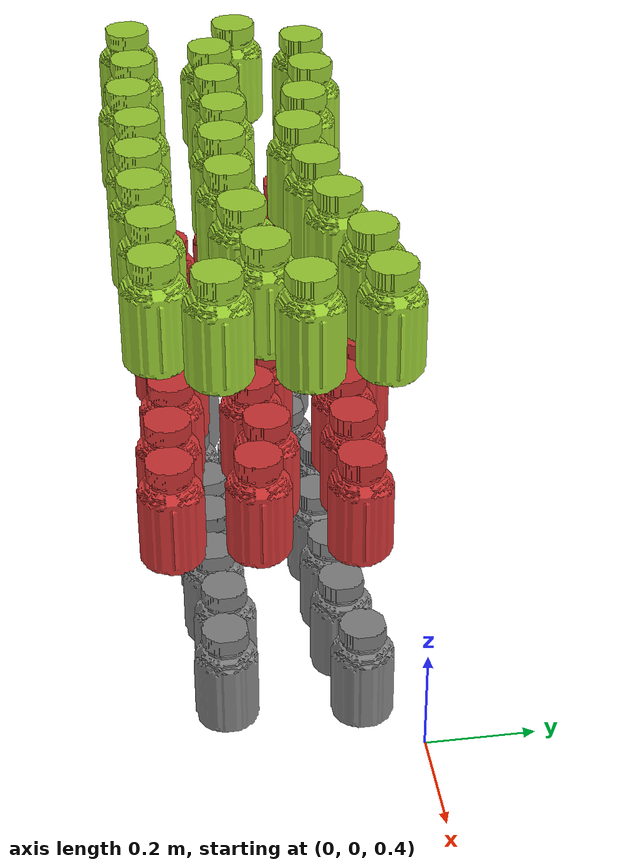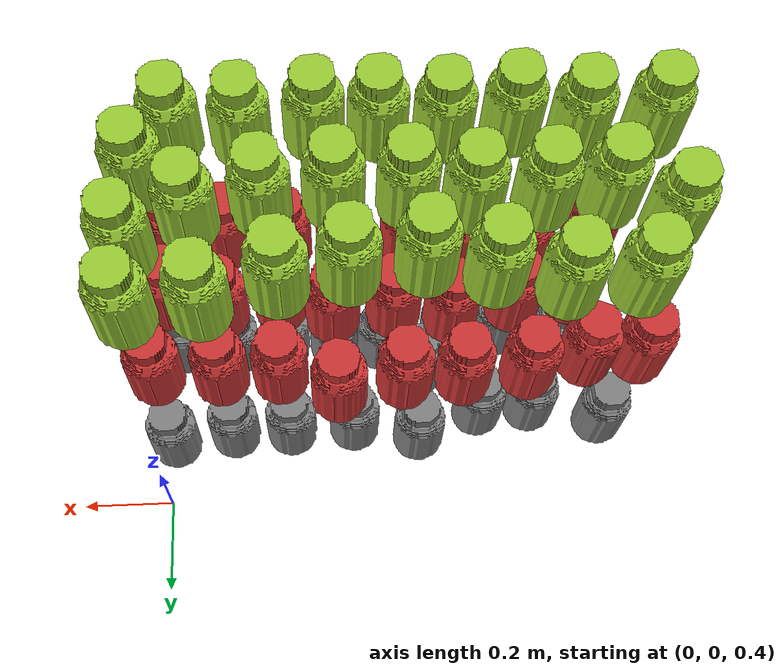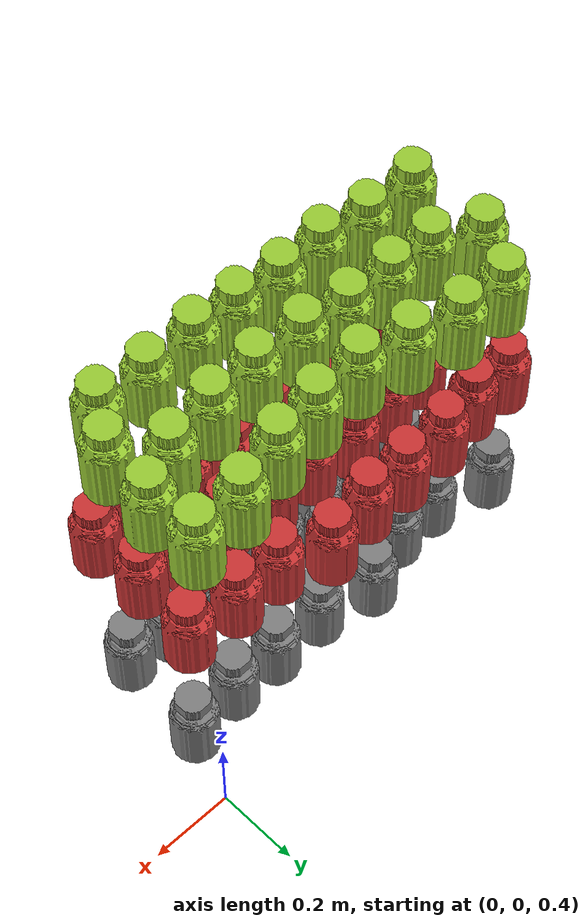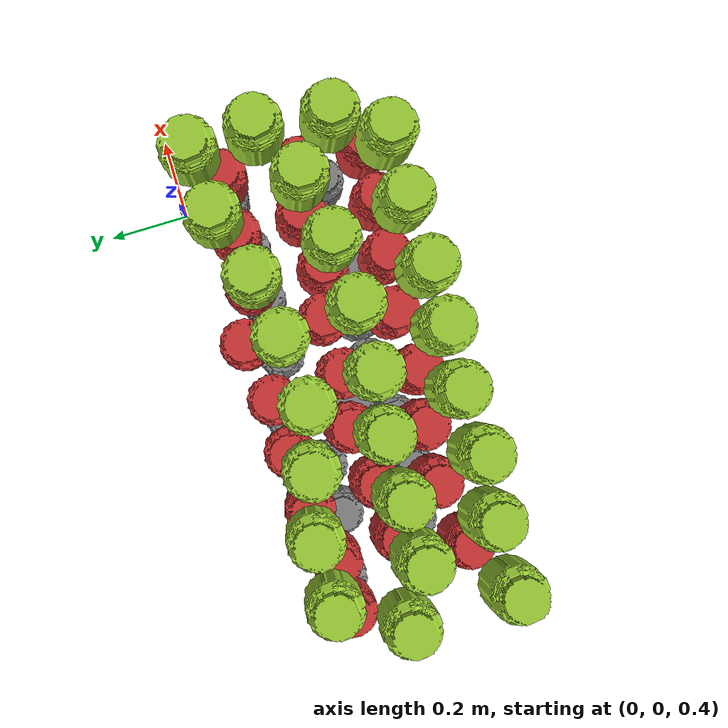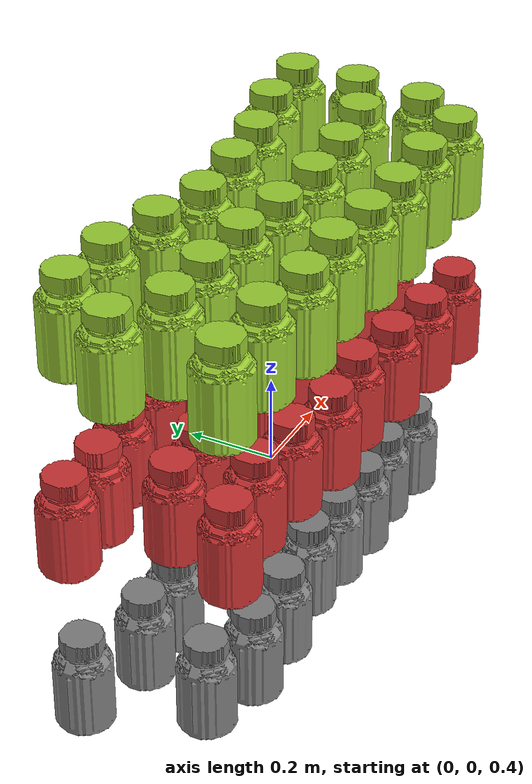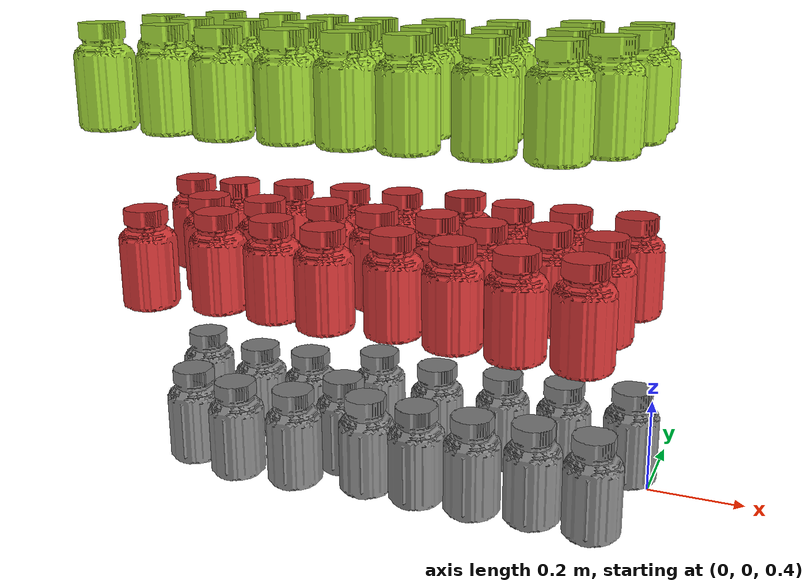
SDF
<sdf version="1.7">
 <world name="default">
  <plugin name="gazebo_ros_factory" filename="libgazebo_ros_factory.so"/>
  <plugin name="attach_detach_plugin" filename="libattach_detach.so"/>
  <gravity>0 0 -9.8</gravity>
  <physics name="default_physics" default="0" type="ode">
   <max_step_size>0.001</max_step_size>
   <real_time_factor>1</real_time_factor>
   <real_time_update_rate>1000</real_time_update_rate>
  </physics>
  <light name="Warehouse_CeilingLight_003" type="point">
   <pose>0 0 9 0 -0 0</pose>
   <diffuse>0.5 0.5 0.5 1</diffuse>
   <specular>0.2 0.2 0.2 1</specular>
   <attenuation>
    <range>80</range>
    <constant>0.3</constant>
    <linear>0.01</linear>
    <quadratic>0.001</quadratic>
   </attenuation>
   <direction>0.1 0.1 -1</direction>
   <spot><inner_angle>0</inner_angle><outer_angle>0</outer_angle><falloff>0</falloff></spot>
  </light>
  <magnetic_field>6e-06 2.3e-05 -4.2e-05</magnetic_field>
  <atmosphere type="adiabatic"/>
  <scene><ambient>0.4 0.4 0.4 1</ambient><background>0.7 0.7 0.7 1</background><shadows>1</shadows></scene>
  <audio><device>default</device></audio>
  <spherical_coordinates>
   <surface_model>EARTH_WGS84</surface_model>
   <latitude_deg>0</latitude_deg>
   <longitude_deg>0</longitude_deg>
   <elevation>0</elevation>
   <heading_deg>0</heading_deg>
  </spherical_coordinates>
  <model name="Medicine_Bottle">
   <static>0</static>
   <link name="medicine_bottle_link">
    <inertial>
     <mass>0.05</mass>
     <inertia><ixx>1e-05</ixx><ixy>0</ixy><ixz>0</ixz><iyy>1e-05</iyy><iyz>0</iyz><izz>1e-05</izz></inertia>
    </inertial>
    <visual name="visual">
     <geometry>
      <mesh><uri>model://Medicine_Bottle/meshes/Medicine_Bottle.stl</uri><scale>0.1 0.1 0.1</scale></mesh>
     </geometry>
     <material>
      <ambient>0.5 0.5 0.5 1</ambient>
      <diffuse>0.5 0.5 0.5 1</diffuse>
      <specular>0.1 0.1 0.1 1</specular>
     </material>
    </visual>
    <collision name="collision">
     <geometry>
      <mesh><uri>model://Medicine_Bottle/meshes/Medicine_Bottle.stl</uri><scale>0.1 0.1 0.1</scale></mesh>
     </geometry>
    </collision>
   </link>
   <pose>-0.021305 -0.111608 0.474978 -0.00016 -0.000412 -3.11408</pose>
  </model>
  <model name="Medicine_Bottle_clone">
   <static>0</static>
   <link name="medicine_bottle_link">
    <inertial>
     <mass>0.05</mass>
     <inertia><ixx>1e-05</ixx><ixy>0</ixy><ixz>0</ixz><iyy>1e-05</iyy><iyz>0</iyz><izz>1e-05</izz></inertia>
    </inertial>
    <visual name="visual">
     <geometry>
      <mesh><uri>model://Medicine_Bottle/meshes/Medicine_Bottle.stl</uri><scale>0.1 0.1 0.1</scale></mesh>
     </geometry>
     <material>
      <ambient>0.5 0.5 0.5 1</ambient>
      <diffuse>0.5 0.5 0.5 1</diffuse>
      <specular>0.1 0.1 0.1 1</specular>
     </material>
    </visual>
    <collision name="collision">
     <geometry>
      <mesh><uri>model://Medicine_Bottle/meshes/Medicine_Bottle.stl</uri><scale>0.1 0.1 0.1</scale></mesh>
     </geometry>
    </collision>
   </link>
   <pose>-0.154694 -0.128691 0.474988 -0.00016 -0.000412 -3.13435</pose>
  </model>
  <model name="Medicine_Bottle_clone_clone">
   <static>0</static>
   <link name="medicine_bottle_link">
    <inertial>
     <mass>0.05</mass>
     <inertia><ixx>1e-05</ixx><ixy>0</ixy><ixz>0</ixz><iyy>1e-05</iyy><iyz>0</iyz><izz>1e-05</izz></inertia>
    </inertial>
    <visual name="visual">
     <geometry>
      <mesh><uri>model://Medicine_Bottle/meshes/Medicine_Bottle.stl</uri><scale>0.1 0.1 0.1</scale></mesh>
     </geometry>
     <material>
      <ambient>0.5 0.5 0.5 1</ambient>
      <diffuse>0.5 0.5 0.5 1</diffuse>
      <specular>0.1 0.1 0.1 1</specular>
     </material>
    </visual>
    <collision name="collision">
     <geometry>
      <mesh><uri>model://Medicine_Bottle/meshes/Medicine_Bottle.stl</uri><scale>0.1 0.1 0.1</scale></mesh>
     </geometry>
    </collision>
   </link>
   <pose>-0.282684 -0.12955 0.474988 -0.00016 -0.000412 -3.11268</pose>
  </model>
  <model name="Medicine_Bottle_clone_clone_0">
   <static>0</static>
   <link name="medicine_bottle_link">
    <inertial>
     <mass>0.05</mass>
     <inertia><ixx>1e-05</ixx><ixy>0</ixy><ixz>0</ixz><iyy>1e-05</iyy><iyz>0</iyz><izz>1e-05</izz></inertia>
    </inertial>
    <visual name="visual">
     <geometry>
      <mesh><uri>model://Medicine_Bottle/meshes/Medicine_Bottle.stl</uri><scale>0.1 0.1 0.1</scale></mesh>
     </geometry>
     <material>
      <ambient>0.5 0.5 0.5 1</ambient>
      <diffuse>0.5 0.5 0.5 1</diffuse>
      <specular>0.1 0.1 0.1 1</specular>
     </material>
    </visual>
    <collision name="collision">
     <geometry>
      <mesh><uri>model://Medicine_Bottle/meshes/Medicine_Bottle.stl</uri><scale>0.1 0.1 0.1</scale></mesh>
     </geometry>
    </collision>
   </link>
   <pose>-0.423724 -0.134793 0.474978 -0.00016 -0.000412 -3.11249</pose>
  </model>
  <model name="Medicine_Bottle_clone_clone_1">
   <static>0</static>
   <link name="medicine_bottle_link">
    <inertial>
     <mass>0.05</mass>
     <inertia><ixx>1e-05</ixx><ixy>0</ixy><ixz>0</ixz><iyy>1e-05</iyy><iyz>0</iyz><izz>1e-05</izz></inertia>
    </inertial>
    <visual name="visual">
     <geometry>
      <mesh><uri>model://Medicine_Bottle/meshes/Medicine_Bottle.stl</uri><scale>0.1 0.1 0.1</scale></mesh>
     </geometry>
     <material>
      <ambient>0.5 0.5 0.5 1</ambient>
      <diffuse>0.5 0.5 0.5 1</diffuse>
      <specular>0.1 0.1 0.1 1</specular>
     </material>
    </visual>
    <collision name="collision">
     <geometry>
      <mesh><uri>model://Medicine_Bottle/meshes/Medicine_Bottle.stl</uri><scale>0.1 0.1 0.1</scale></mesh>
     </geometry>
    </collision>
   </link>
   <pose>-0.566814 -0.106112 0.474988 -0.00016 -0.000412 -3.11289</pose>
  </model>
  <model name="Medicine_Bottle_clone_clone_2">
   <static>0</static>
   <link name="medicine_bottle_link">
    <inertial>
     <mass>0.05</mass>
     <inertia><ixx>1e-05</ixx><ixy>0</ixy><ixz>0</ixz><iyy>1e-05</iyy><iyz>0</iyz><izz>1e-05</izz></inertia>
    </inertial>
    <visual name="visual">
     <geometry>
      <mesh><uri>model://Medicine_Bottle/meshes/Medicine_Bottle.stl</uri><scale>0.1 0.1 0.1</scale></mesh>
     </geometry>
     <material>
      <ambient>0.5 0.5 0.5 1</ambient>
      <diffuse>0.5 0.5 0.5 1</diffuse>
      <specular>0.1 0.1 0.1 1</specular>
     </material>
    </visual>
    <collision name="collision">
     <geometry>
      <mesh><uri>model://Medicine_Bottle/meshes/Medicine_Bottle.stl</uri><scale>0.1 0.1 0.1</scale></mesh>
     </geometry>
    </collision>
   </link>
   <pose>-0.704865 -0.159406 0.474988 -0.00016 -0.000412 -3.11308</pose>
  </model>
  <model name="Medicine_Bottle_clone_clone_3">
   <static>0</static>
   <link name="medicine_bottle_link">
    <inertial>
     <mass>0.05</mass>
     <inertia><ixx>1e-05</ixx><ixy>0</ixy><ixz>0</ixz><iyy>1e-05</iyy><iyz>0</iyz><izz>1e-05</izz></inertia>
    </inertial>
    <visual name="visual">
     <geometry>
      <mesh><uri>model://Medicine_Bottle/meshes/Medicine_Bottle.stl</uri><scale>0.1 0.1 0.1</scale></mesh>
     </geometry>
     <material>
      <ambient>0.5 0.5 0.5 1</ambient>
      <diffuse>0.5 0.5 0.5 1</diffuse>
      <specular>0.1 0.1 0.1 1</specular>
     </material>
    </visual>
    <collision name="collision">
     <geometry>
      <mesh><uri>model://Medicine_Bottle/meshes/Medicine_Bottle.stl</uri><scale>0.1 0.1 0.1</scale></mesh>
     </geometry>
    </collision>
   </link>
   <pose>-0.042868 -0.345663 0.474988 -0.00016 -0.000412 -3.11242</pose>
  </model>
  <model name="Medicine_Bottle_clone_clone_2_clone">
   <static>0</static>
   <link name="medicine_bottle_link">
    <inertial>
     <mass>0.05</mass>
     <inertia><ixx>1e-05</ixx><ixy>0</ixy><ixz>0</ixz><iyy>1e-05</iyy><iyz>0</iyz><izz>1e-05</izz></inertia>
    </inertial>
    <visual name="visual">
     <geometry>
      <mesh><uri>model://Medicine_Bottle/meshes/Medicine_Bottle.stl</uri><scale>0.1 0.1 0.1</scale></mesh>
     </geometry>
     <material>
      <ambient>0.5 0.5 0.5 1</ambient>
      <diffuse>0.5 0.5 0.5 1</diffuse>
      <specular>0.1 0.1 0.1 1</specular>
     </material>
    </visual>
    <collision name="collision">
     <geometry>
      <mesh><uri>model://Medicine_Bottle/meshes/Medicine_Bottle.stl</uri><scale>0.1 0.1 0.1</scale></mesh>
     </geometry>
    </collision>
   </link>
   <pose>-0.1584 -0.335335 0.474978 -0.00016 -0.000412 -3.11812</pose>
  </model>
  <model name="Medicine_Bottle_clone_clone_2_clone_0">
   <static>0</static>
   <link name="medicine_bottle_link">
    <inertial>
     <mass>0.05</mass>
     <inertia><ixx>1e-05</ixx><ixy>0</ixy><ixz>0</ixz><iyy>1e-05</iyy><iyz>0</iyz><izz>1e-05</izz></inertia>
    </inertial>
    <visual name="visual">
     <geometry>
      <mesh><uri>model://Medicine_Bottle/meshes/Medicine_Bottle.stl</uri><scale>0.1 0.1 0.1</scale></mesh>
     </geometry>
     <material>
      <ambient>0.5 0.5 0.5 1</ambient>
      <diffuse>0.5 0.5 0.5 1</diffuse>
      <specular>0.1 0.1 0.1 1</specular>
     </material>
    </visual>
    <collision name="collision">
     <geometry>
      <mesh><uri>model://Medicine_Bottle/meshes/Medicine_Bottle.stl</uri><scale>0.1 0.1 0.1</scale></mesh>
     </geometry>
    </collision>
   </link>
   <pose>-0.27351 -0.343876 0.474988 -0.00016 -0.000412 -3.13733</pose>
  </model>
  <model name="Medicine_Bottle_clone_clone_2_clone_1">
   <static>0</static>
   <link name="medicine_bottle_link">
    <inertial>
     <mass>0.05</mass>
     <inertia><ixx>1e-05</ixx><ixy>0</ixy><ixz>0</ixz><iyy>1e-05</iyy><iyz>0</iyz><izz>1e-05</izz></inertia>
    </inertial>
    <visual name="visual">
     <geometry>
      <mesh><uri>model://Medicine_Bottle/meshes/Medicine_Bottle.stl</uri><scale>0.1 0.1 0.1</scale></mesh>
     </geometry>
     <material>
      <ambient>0.5 0.5 0.5 1</ambient>
      <diffuse>0.5 0.5 0.5 1</diffuse>
      <specular>0.1 0.1 0.1 1</specular>
     </material>
    </visual>
    <collision name="collision">
     <geometry>
      <mesh><uri>model://Medicine_Bottle/meshes/Medicine_Bottle.stl</uri><scale>0.1 0.1 0.1</scale></mesh>
     </geometry>
    </collision>
   </link>
   <pose>-0.387059 -0.340507 0.474988 -0.000157 -0.000458 3.01582</pose>
  </model>
  <model name="Medicine_Bottle_clone_clone_2_clone_2">
   <static>0</static>
   <link name="medicine_bottle_link">
    <inertial>
     <mass>0.05</mass>
     <inertia><ixx>1e-05</ixx><ixy>0</ixy><ixz>0</ixz><iyy>1e-05</iyy><iyz>0</iyz><izz>1e-05</izz></inertia>
    </inertial>
    <visual name="visual">
     <geometry>
      <mesh><uri>model://Medicine_Bottle/meshes/Medicine_Bottle.stl</uri><scale>0.1 0.1 0.1</scale></mesh>
     </geometry>
     <material>
      <ambient>0.5 0.5 0.5 1</ambient>
      <diffuse>0.5 0.5 0.5 1</diffuse>
      <specular>0.1 0.1 0.1 1</specular>
     </material>
    </visual>
    <collision name="collision">
     <geometry>
      <mesh><uri>model://Medicine_Bottle/meshes/Medicine_Bottle.stl</uri><scale>0.1 0.1 0.1</scale></mesh>
     </geometry>
    </collision>
   </link>
   <pose>-0.495091 -0.334484 0.474978 -0.000132 -0.000304 -2.94442</pose>
  </model>
  <model name="Medicine_Bottle_clone_clone_2_clone_3">
   <static>0</static>
   <link name="medicine_bottle_link">
    <inertial>
     <mass>0.05</mass>
     <inertia><ixx>1e-05</ixx><ixy>0</ixy><ixz>0</ixz><iyy>1e-05</iyy><iyz>0</iyz><izz>1e-05</izz></inertia>
    </inertial>
    <visual name="visual">
     <geometry>
      <mesh><uri>model://Medicine_Bottle/meshes/Medicine_Bottle.stl</uri><scale>0.1 0.1 0.1</scale></mesh>
     </geometry>
     <material>
      <ambient>0.5 0.5 0.5 1</ambient>
      <diffuse>0.5 0.5 0.5 1</diffuse>
      <specular>0.1 0.1 0.1 1</specular>
     </material>
    </visual>
    <collision name="collision">
     <geometry>
      <mesh><uri>model://Medicine_Bottle/meshes/Medicine_Bottle.stl</uri><scale>0.1 0.1 0.1</scale></mesh>
     </geometry>
    </collision>
   </link>
   <pose>-0.577068 -0.263632 0.474988 -0.00016 -0.000412 3.0867</pose>
  </model>
  <model name="Medicine_Bottle_clone_clone_2_clone_4">
   <static>0</static>
   <link name="medicine_bottle_link">
    <inertial>
     <mass>0.05</mass>
     <inertia><ixx>1e-05</ixx><ixy>0</ixy><ixz>0</ixz><iyy>1e-05</iyy><iyz>0</iyz><izz>1e-05</izz></inertia>
    </inertial>
    <visual name="visual">
     <geometry>
      <mesh><uri>model://Medicine_Bottle/meshes/Medicine_Bottle.stl</uri><scale>0.1 0.1 0.1</scale></mesh>
     </geometry>
     <material>
      <ambient>0.5 0.5 0.5 1</ambient>
      <diffuse>0.5 0.5 0.5 1</diffuse>
      <specular>0.1 0.1 0.1 1</specular>
     </material>
    </visual>
    <collision name="collision">
     <geometry>
      <mesh><uri>model://Medicine_Bottle/meshes/Medicine_Bottle.stl</uri><scale>0.1 0.1 0.1</scale></mesh>
     </geometry>
    </collision>
   </link>
   <pose>-0.769506 -0.360302 0.474988 -0.00016 -0.000412 -3.11247</pose>
  </model>
  <model name="Medicine_Bottle_clone_clone_2_clone_5">
   <static>0</static>
   <link name="medicine_bottle_link">
    <inertial>
     <mass>0.05</mass>
     <inertia><ixx>1e-05</ixx><ixy>0</ixy><ixz>0</ixz><iyy>1e-05</iyy><iyz>0</iyz><izz>1e-05</izz></inertia>
    </inertial>
    <visual name="visual">
     <geometry>
      <mesh><uri>model://Medicine_Bottle/meshes/Medicine_Bottle.stl</uri><scale>0.1 0.1 0.1</scale></mesh>
     </geometry>
     <material>
      <ambient>0.5 0.5 0.5 1</ambient>
      <diffuse>0.5 0.5 0.5 1</diffuse>
      <specular>0.1 0.1 0.1 1</specular>
     </material>
    </visual>
    <collision name="collision">
     <geometry>
      <mesh><uri>model://Medicine_Bottle/meshes/Medicine_Bottle.stl</uri><scale>0.1 0.1 0.1</scale></mesh>
     </geometry>
    </collision>
   </link>
   <pose>-0.642489 -0.355211 0.474978 -0.00016 -0.000412 -3.07593</pose>
  </model>
  <model name="Medicine_Bottle_0">
   <static>0</static>
   <link name="medicine_bottle_link">
    <inertial>
     <mass>0.05</mass>
     <inertia><ixx>1e-05</ixx><ixy>0</ixy><ixz>0</ixz><iyy>1e-05</iyy><iyz>0</iyz><izz>1e-05</izz></inertia>
    </inertial>
    <visual name="visual">
     <geometry>
      <mesh><uri>model://Medicine_Bottle/meshes/Medicine_Bottle.stl</uri><scale>0.1 0.1 0.1</scale></mesh>
     </geometry>
     <material>
      <ambient>0.4 0.1 0.1 1</ambient>
      <diffuse>0.8 0.2 0.2 1</diffuse>
      <specular>0.2 0.1 0.1 1</specular>
     </material>
    </visual>
    <collision name="collision">
     <geometry>
      <mesh><uri>model://Medicine_Bottle/meshes/Medicine_Bottle.stl</uri><scale>0.1 0.1 0.1</scale></mesh>
     </geometry>
    </collision>
   </link>
   <pose>-0.030014 -0.116842 0.824988 -0.00016 -0.000412 -0.000384</pose>
  </model>
  <model name="Medicine_Bottle_0_clone">
   <static>0</static>
   <link name="medicine_bottle_link">
    <inertial>
     <mass>0.05</mass>
     <inertia><ixx>1e-05</ixx><ixy>0</ixy><ixz>0</ixz><iyy>1e-05</iyy><iyz>0</iyz><izz>1e-05</izz></inertia>
    </inertial>
    <visual name="visual">
     <geometry>
      <mesh><uri>model://Medicine_Bottle/meshes/Medicine_Bottle.stl</uri><scale>0.1 0.1 0.1</scale></mesh>
     </geometry>
     <material>
      <ambient>0.4 0.1 0.1 1</ambient>
      <diffuse>0.8 0.2 0.2 1</diffuse>
      <specular>0.2 0.1 0.1 1</specular>
     </material>
    </visual>
    <collision name="collision">
     <geometry>
      <mesh><uri>model://Medicine_Bottle/meshes/Medicine_Bottle.stl</uri><scale>0.1 0.1 0.1</scale></mesh>
     </geometry>
    </collision>
   </link>
   <pose>-0.158171 -0.110383 0.824988 -0.00016 -0.000412 -0.002833</pose>
  </model>
  <model name="Medicine_Bottle_0_clone_0">
   <static>0</static>
   <link name="medicine_bottle_link">
    <inertial>
     <mass>0.05</mass>
     <inertia><ixx>1e-05</ixx><ixy>0</ixy><ixz>0</ixz><iyy>1e-05</iyy><iyz>0</iyz><izz>1e-05</izz></inertia>
    </inertial>
    <visual name="visual">
     <geometry>
      <mesh><uri>model://Medicine_Bottle/meshes/Medicine_Bottle.stl</uri><scale>0.1 0.1 0.1</scale></mesh>
     </geometry>
     <material>
      <ambient>0.4 0.1 0.1 1</ambient>
      <diffuse>0.8 0.2 0.2 1</diffuse>
      <specular>0.2 0.1 0.1 1</specular>
     </material>
    </visual>
    <collision name="collision">
     <geometry>
      <mesh><uri>model://Medicine_Bottle/meshes/Medicine_Bottle.stl</uri><scale>0.1 0.1 0.1</scale></mesh>
     </geometry>
    </collision>
   </link>
   <pose>-0.291166 -0.405783 0.824987 -0.00016 -0.000412 -0.000384</pose>
  </model>
  <model name="Medicine_Bottle_0_clone_1">
   <static>0</static>
   <link name="medicine_bottle_link">
    <inertial>
     <mass>0.05</mass>
     <inertia><ixx>1e-05</ixx><ixy>0</ixy><ixz>0</ixz><iyy>1e-05</iyy><iyz>0</iyz><izz>1e-05</izz></inertia>
    </inertial>
    <visual name="visual">
     <geometry>
      <mesh><uri>model://Medicine_Bottle/meshes/Medicine_Bottle.stl</uri><scale>0.1 0.1 0.1</scale></mesh>
     </geometry>
     <material>
      <ambient>0.4 0.1 0.1 1</ambient>
      <diffuse>0.8 0.2 0.2 1</diffuse>
      <specular>0.2 0.1 0.1 1</specular>
     </material>
    </visual>
    <collision name="collision">
     <geometry>
      <mesh><uri>model://Medicine_Bottle/meshes/Medicine_Bottle.stl</uri><scale>0.1 0.1 0.1</scale></mesh>
     </geometry>
    </collision>
   </link>
   <pose>-0.411783 -0.386617 0.824988 -0.00016 -0.000412 -0.000384</pose>
  </model>
  <model name="Medicine_Bottle_0_clone_2">
   <static>0</static>
   <link name="medicine_bottle_link">
    <inertial>
     <mass>0.05</mass>
     <inertia><ixx>1e-05</ixx><ixy>0</ixy><ixz>0</ixz><iyy>1e-05</iyy><iyz>0</iyz><izz>1e-05</izz></inertia>
    </inertial>
    <visual name="visual">
     <geometry>
      <mesh><uri>model://Medicine_Bottle/meshes/Medicine_Bottle.stl</uri><scale>0.1 0.1 0.1</scale></mesh>
     </geometry>
     <material>
      <ambient>0.4 0.1 0.1 1</ambient>
      <diffuse>0.8 0.2 0.2 1</diffuse>
      <specular>0.2 0.1 0.1 1</specular>
     </material>
    </visual>
    <collision name="collision">
     <geometry>
      <mesh><uri>model://Medicine_Bottle/meshes/Medicine_Bottle.stl</uri><scale>0.1 0.1 0.1</scale></mesh>
     </geometry>
    </collision>
   </link>
   <pose>-0.159362 -0.25593 0.824978 -0.00016 -0.000412 0.003182</pose>
  </model>
  <model name="Medicine_Bottle_0_clone_3">
   <static>0</static>
   <link name="medicine_bottle_link">
    <inertial>
     <mass>0.05</mass>
     <inertia><ixx>1e-05</ixx><ixy>0</ixy><ixz>0</ixz><iyy>1e-05</iyy><iyz>0</iyz><izz>1e-05</izz></inertia>
    </inertial>
    <visual name="visual">
     <geometry>
      <mesh><uri>model://Medicine_Bottle/meshes/Medicine_Bottle.stl</uri><scale>0.1 0.1 0.1</scale></mesh>
     </geometry>
     <material>
      <ambient>0.4 0.1 0.1 1</ambient>
      <diffuse>0.8 0.2 0.2 1</diffuse>
      <specular>0.2 0.1 0.1 1</specular>
     </material>
    </visual>
    <collision name="collision">
     <geometry>
      <mesh><uri>model://Medicine_Bottle/meshes/Medicine_Bottle.stl</uri><scale>0.1 0.1 0.1</scale></mesh>
     </geometry>
    </collision>
   </link>
   <pose>-0.050368 -0.282769 0.824988 -0.00016 -0.000412 -0.000384</pose>
  </model>
  <model name="Medicine_Bottle_0_clone_4">
   <static>0</static>
   <link name="medicine_bottle_link">
    <inertial>
     <mass>0.05</mass>
     <inertia><ixx>1e-05</ixx><ixy>0</ixy><ixz>0</ixz><iyy>1e-05</iyy><iyz>0</iyz><izz>1e-05</izz></inertia>
    </inertial>
    <visual name="visual">
     <geometry>
      <mesh><uri>model://Medicine_Bottle/meshes/Medicine_Bottle.stl</uri><scale>0.1 0.1 0.1</scale></mesh>
     </geometry>
     <material>
      <ambient>0.4 0.1 0.1 1</ambient>
      <diffuse>0.8 0.2 0.2 1</diffuse>
      <specular>0.2 0.1 0.1 1</specular>
     </material>
    </visual>
    <collision name="collision">
     <geometry>
      <mesh><uri>model://Medicine_Bottle/meshes/Medicine_Bottle.stl</uri><scale>0.1 0.1 0.1</scale></mesh>
     </geometry>
    </collision>
   </link>
   <pose>-0.278604 -0.268851 0.824988 -0.00016 -0.000412 -0.000699</pose>
  </model>
  <model name="Medicine_Bottle_0_clone_5">
   <static>0</static>
   <link name="medicine_bottle_link">
    <inertial>
     <mass>0.05</mass>
     <inertia><ixx>1e-05</ixx><ixy>0</ixy><ixz>0</ixz><iyy>1e-05</iyy><iyz>0</iyz><izz>1e-05</izz></inertia>
    </inertial>
    <visual name="visual">
     <geometry>
      <mesh><uri>model://Medicine_Bottle/meshes/Medicine_Bottle.stl</uri><scale>0.1 0.1 0.1</scale></mesh>
     </geometry>
     <material>
      <ambient>0.4 0.1 0.1 1</ambient>
      <diffuse>0.8 0.2 0.2 1</diffuse>
      <specular>0.2 0.1 0.1 1</specular>
     </material>
    </visual>
    <collision name="collision">
     <geometry>
      <mesh><uri>model://Medicine_Bottle/meshes/Medicine_Bottle.stl</uri><scale>0.1 0.1 0.1</scale></mesh>
     </geometry>
    </collision>
   </link>
   <pose>-0.275642 -0.108979 0.824988 -0.00016 -0.000412 -0.000384</pose>
  </model>
  <model name="Medicine_Bottle_0_clone_6">
   <static>0</static>
   <link name="medicine_bottle_link">
    <inertial>
     <mass>0.05</mass>
     <inertia><ixx>1e-05</ixx><ixy>0</ixy><ixz>0</ixz><iyy>1e-05</iyy><iyz>0</iyz><izz>1e-05</izz></inertia>
    </inertial>
    <visual name="visual">
     <geometry>
      <mesh><uri>model://Medicine_Bottle/meshes/Medicine_Bottle.stl</uri><scale>0.1 0.1 0.1</scale></mesh>
     </geometry>
     <material>
      <ambient>0.4 0.1 0.1 1</ambient>
      <diffuse>0.8 0.2 0.2 1</diffuse>
      <specular>0.2 0.1 0.1 1</specular>
     </material>
    </visual>
    <collision name="collision">
     <geometry>
      <mesh><uri>model://Medicine_Bottle/meshes/Medicine_Bottle.stl</uri><scale>0.1 0.1 0.1</scale></mesh>
     </geometry>
    </collision>
   </link>
   <pose>-0.383758 -0.239182 0.824988 -0.00016 -0.000412 -0.040425</pose>
  </model>
  <model name="Medicine_Bottle_0_clone_7">
   <static>0</static>
   <link name="medicine_bottle_link">
    <inertial>
     <mass>0.05</mass>
     <inertia><ixx>1e-05</ixx><ixy>0</ixy><ixz>0</ixz><iyy>1e-05</iyy><iyz>0</iyz><izz>1e-05</izz></inertia>
    </inertial>
    <visual name="visual">
     <geometry>
      <mesh><uri>model://Medicine_Bottle/meshes/Medicine_Bottle.stl</uri><scale>0.1 0.1 0.1</scale></mesh>
     </geometry>
     <material>
      <ambient>0.4 0.1 0.1 1</ambient>
      <diffuse>0.8 0.2 0.2 1</diffuse>
      <specular>0.2 0.1 0.1 1</specular>
     </material>
    </visual>
    <collision name="collision">
     <geometry>
      <mesh><uri>model://Medicine_Bottle/meshes/Medicine_Bottle.stl</uri><scale>0.1 0.1 0.1</scale></mesh>
     </geometry>
    </collision>
   </link>
   <pose>-0.389292 -0.064966 0.824988 -0.00016 -0.000412 -0.240456</pose>
  </model>
  <model name="Medicine_Bottle_0_clone_8">
   <static>0</static>
   <link name="medicine_bottle_link">
    <inertial>
     <mass>0.05</mass>
     <inertia><ixx>1e-05</ixx><ixy>0</ixy><ixz>0</ixz><iyy>1e-05</iyy><iyz>0</iyz><izz>1e-05</izz></inertia>
    </inertial>
    <visual name="visual">
     <geometry>
      <mesh><uri>model://Medicine_Bottle/meshes/Medicine_Bottle.stl</uri><scale>0.1 0.1 0.1</scale></mesh>
     </geometry>
     <material>
      <ambient>0.4 0.1 0.1 1</ambient>
      <diffuse>0.8 0.2 0.2 1</diffuse>
      <specular>0.2 0.1 0.1 1</specular>
     </material>
    </visual>
    <collision name="collision">
     <geometry>
      <mesh><uri>model://Medicine_Bottle/meshes/Medicine_Bottle.stl</uri><scale>0.1 0.1 0.1</scale></mesh>
     </geometry>
    </collision>
   </link>
   <pose>-0.052274 -0.426727 0.824988 -0.00016 -0.000412 -0.000384</pose>
  </model>
  <model name="Medicine_Bottle_0_clone_9">
   <static>0</static>
   <link name="medicine_bottle_link">
    <inertial>
     <mass>0.05</mass>
     <inertia><ixx>1e-05</ixx><ixy>0</ixy><ixz>0</ixz><iyy>1e-05</iyy><iyz>0</iyz><izz>1e-05</izz></inertia>
    </inertial>
    <visual name="visual">
     <geometry>
      <mesh><uri>model://Medicine_Bottle/meshes/Medicine_Bottle.stl</uri><scale>0.1 0.1 0.1</scale></mesh>
     </geometry>
     <material>
      <ambient>0.4 0.1 0.1 1</ambient>
      <diffuse>0.8 0.2 0.2 1</diffuse>
      <specular>0.2 0.1 0.1 1</specular>
     </material>
    </visual>
    <collision name="collision">
     <geometry>
      <mesh><uri>model://Medicine_Bottle/meshes/Medicine_Bottle.stl</uri><scale>0.1 0.1 0.1</scale></mesh>
     </geometry>
    </collision>
   </link>
   <pose>-0.171443 -0.420345 0.824988 -0.00016 -0.000412 -0.000384</pose>
  </model>
  <model name="Medicine_Bottle_0_clone_1_clone">
   <static>0</static>
   <link name="medicine_bottle_link">
    <inertial>
     <mass>0.05</mass>
     <inertia><ixx>1e-05</ixx><ixy>0</ixy><ixz>0</ixz><iyy>1e-05</iyy><iyz>0</iyz><izz>1e-05</izz></inertia>
    </inertial>
    <visual name="visual">
     <geometry>
      <mesh><uri>model://Medicine_Bottle/meshes/Medicine_Bottle.stl</uri><scale>0.1 0.1 0.1</scale></mesh>
     </geometry>
     <material>
      <ambient>0.4 0.1 0.1 1</ambient>
      <diffuse>0.8 0.2 0.2 1</diffuse>
      <specular>0.2 0.1 0.1 1</specular>
     </material>
    </visual>
    <collision name="collision">
     <geometry>
      <mesh><uri>model://Medicine_Bottle/meshes/Medicine_Bottle.stl</uri><scale>0.1 0.1 0.1</scale></mesh>
     </geometry>
    </collision>
   </link>
   <pose>-0.518437 -0.087516 0.824988 -0.00016 -0.000412 -0.000384</pose>
  </model>
  <model name="Medicine_Bottle_0_clone_1_clone_0">
   <static>0</static>
   <link name="medicine_bottle_link">
    <inertial>
     <mass>0.05</mass>
     <inertia><ixx>1e-05</ixx><ixy>0</ixy><ixz>0</ixz><iyy>1e-05</iyy><iyz>0</iyz><izz>1e-05</izz></inertia>
    </inertial>
    <visual name="visual">
     <geometry>
      <mesh><uri>model://Medicine_Bottle/meshes/Medicine_Bottle.stl</uri><scale>0.1 0.1 0.1</scale></mesh>
     </geometry>
     <material>
      <ambient>0.4 0.1 0.1 1</ambient>
      <diffuse>0.8 0.2 0.2 1</diffuse>
      <specular>0.2 0.1 0.1 1</specular>
     </material>
    </visual>
    <collision name="collision">
     <geometry>
      <mesh><uri>model://Medicine_Bottle/meshes/Medicine_Bottle.stl</uri><scale>0.1 0.1 0.1</scale></mesh>
     </geometry>
    </collision>
   </link>
   <pose>-0.634953 -0.090202 0.824988 -0.00016 -0.000412 -0.000384</pose>
  </model>
  <model name="Medicine_Bottle_0_clone_1_clone_1">
   <static>0</static>
   <link name="medicine_bottle_link">
    <inertial>
     <mass>0.05</mass>
     <inertia><ixx>1e-05</ixx><ixy>0</ixy><ixz>0</ixz><iyy>1e-05</iyy><iyz>0</iyz><izz>1e-05</izz></inertia>
    </inertial>
    <visual name="visual">
     <geometry>
      <mesh><uri>model://Medicine_Bottle/meshes/Medicine_Bottle.stl</uri><scale>0.1 0.1 0.1</scale></mesh>
     </geometry>
     <material>
      <ambient>0.4 0.1 0.1 1</ambient>
      <diffuse>0.8 0.2 0.2 1</diffuse>
      <specular>0.2 0.1 0.1 1</specular>
     </material>
    </visual>
    <collision name="collision">
     <geometry>
      <mesh><uri>model://Medicine_Bottle/meshes/Medicine_Bottle.stl</uri><scale>0.1 0.1 0.1</scale></mesh>
     </geometry>
    </collision>
   </link>
   <pose>-0.763671 -0.097504 0.824988 -0.00016 -0.000412 -0.087052</pose>
  </model>
  <model name="Medicine_Bottle_0_clone_1_clone_2">
   <static>0</static>
   <link name="medicine_bottle_link">
    <inertial>
     <mass>0.05</mass>
     <inertia><ixx>1e-05</ixx><ixy>0</ixy><ixz>0</ixz><iyy>1e-05</iyy><iyz>0</iyz><izz>1e-05</izz></inertia>
    </inertial>
    <visual name="visual">
     <geometry>
      <mesh><uri>model://Medicine_Bottle/meshes/Medicine_Bottle.stl</uri><scale>0.1 0.1 0.1</scale></mesh>
     </geometry>
     <material>
      <ambient>0.4 0.1 0.1 1</ambient>
      <diffuse>0.8 0.2 0.2 1</diffuse>
      <specular>0.2 0.1 0.1 1</specular>
     </material>
    </visual>
    <collision name="collision">
     <geometry>
      <mesh><uri>model://Medicine_Bottle/meshes/Medicine_Bottle.stl</uri><scale>0.1 0.1 0.1</scale></mesh>
     </geometry>
    </collision>
   </link>
   <pose>-0.880724 -0.120645 0.824978 2.8e-05 -0.000838 -0.419503</pose>
  </model>
  <model name="Medicine_Bottle_0_clone_1_clone_3">
   <static>0</static>
   <link name="medicine_bottle_link">
    <inertial>
     <mass>0.05</mass>
     <inertia><ixx>1e-05</ixx><ixy>0</ixy><ixz>0</ixz><iyy>1e-05</iyy><iyz>0</iyz><izz>1e-05</izz></inertia>
    </inertial>
    <visual name="visual">
     <geometry>
      <mesh><uri>model://Medicine_Bottle/meshes/Medicine_Bottle.stl</uri><scale>0.1 0.1 0.1</scale></mesh>
     </geometry>
     <material>
      <ambient>0.4 0.1 0.1 1</ambient>
      <diffuse>0.8 0.2 0.2 1</diffuse>
      <specular>0.2 0.1 0.1 1</specular>
     </material>
    </visual>
    <collision name="collision">
     <geometry>
      <mesh><uri>model://Medicine_Bottle/meshes/Medicine_Bottle.stl</uri><scale>0.1 0.1 0.1</scale></mesh>
     </geometry>
    </collision>
   </link>
   <pose>-0.506089 -0.243709 0.824988 -0.00016 -0.000412 -0.000384</pose>
  </model>
  <model name="Medicine_Bottle_0_clone_1_clone_4">
   <static>0</static>
   <link name="medicine_bottle_link">
    <inertial>
     <mass>0.05</mass>
     <inertia><ixx>1e-05</ixx><ixy>0</ixy><ixz>0</ixz><iyy>1e-05</iyy><iyz>0</iyz><izz>1e-05</izz></inertia>
    </inertial>
    <visual name="visual">
     <geometry>
      <mesh><uri>model://Medicine_Bottle/meshes/Medicine_Bottle.stl</uri><scale>0.1 0.1 0.1</scale></mesh>
     </geometry>
     <material>
      <ambient>0.4 0.1 0.1 1</ambient>
      <diffuse>0.8 0.2 0.2 1</diffuse>
      <specular>0.2 0.1 0.1 1</specular>
     </material>
    </visual>
    <collision name="collision">
     <geometry>
      <mesh><uri>model://Medicine_Bottle/meshes/Medicine_Bottle.stl</uri><scale>0.1 0.1 0.1</scale></mesh>
     </geometry>
    </collision>
   </link>
   <pose>-0.620644 -0.227937 0.824988 -0.00016 -0.000412 -0.000384</pose>
  </model>
  <model name="Medicine_Bottle_0_clone_1_clone_5">
   <static>0</static>
   <link name="medicine_bottle_link">
    <inertial>
     <mass>0.05</mass>
     <inertia><ixx>1e-05</ixx><ixy>0</ixy><ixz>0</ixz><iyy>1e-05</iyy><iyz>0</iyz><izz>1e-05</izz></inertia>
    </inertial>
    <visual name="visual">
     <geometry>
      <mesh><uri>model://Medicine_Bottle/meshes/Medicine_Bottle.stl</uri><scale>0.1 0.1 0.1</scale></mesh>
     </geometry>
     <material>
      <ambient>0.4 0.1 0.1 1</ambient>
      <diffuse>0.8 0.2 0.2 1</diffuse>
      <specular>0.2 0.1 0.1 1</specular>
     </material>
    </visual>
    <collision name="collision">
     <geometry>
      <mesh><uri>model://Medicine_Bottle/meshes/Medicine_Bottle.stl</uri><scale>0.1 0.1 0.1</scale></mesh>
     </geometry>
    </collision>
   </link>
   <pose>-0.747807 -0.248275 0.824978 -0.00016 -0.000412 -0.000384</pose>
  </model>
  <model name="Medicine_Bottle_0_clone_1_clone_6">
   <static>0</static>
   <link name="medicine_bottle_link">
    <inertial>
     <mass>0.05</mass>
     <inertia><ixx>1e-05</ixx><ixy>0</ixy><ixz>0</ixz><iyy>1e-05</iyy><iyz>0</iyz><izz>1e-05</izz></inertia>
    </inertial>
    <visual name="visual">
     <geometry>
      <mesh><uri>model://Medicine_Bottle/meshes/Medicine_Bottle.stl</uri><scale>0.1 0.1 0.1</scale></mesh>
     </geometry>
     <material>
      <ambient>0.4 0.1 0.1 1</ambient>
      <diffuse>0.8 0.2 0.2 1</diffuse>
      <specular>0.2 0.1 0.1 1</specular>
     </material>
    </visual>
    <collision name="collision">
     <geometry>
      <mesh><uri>model://Medicine_Bottle/meshes/Medicine_Bottle.stl</uri><scale>0.1 0.1 0.1</scale></mesh>
     </geometry>
    </collision>
   </link>
   <pose>-0.867987 -0.260686 0.824978 -0.00016 -0.000412 -0.001904</pose>
  </model>
  <model name="Medicine_Bottle_0_clone_1_clone_7">
   <static>0</static>
   <link name="medicine_bottle_link">
    <inertial>
     <mass>0.05</mass>
     <inertia><ixx>1e-05</ixx><ixy>0</ixy><ixz>0</ixz><iyy>1e-05</iyy><iyz>0</iyz><izz>1e-05</izz></inertia>
    </inertial>
    <visual name="visual">
     <geometry>
      <mesh><uri>model://Medicine_Bottle/meshes/Medicine_Bottle.stl</uri><scale>0.1 0.1 0.1</scale></mesh>
     </geometry>
     <material>
      <ambient>0.4 0.1 0.1 1</ambient>
      <diffuse>0.8 0.2 0.2 1</diffuse>
      <specular>0.2 0.1 0.1 1</specular>
     </material>
    </visual>
    <collision name="collision">
     <geometry>
      <mesh><uri>model://Medicine_Bottle/meshes/Medicine_Bottle.stl</uri><scale>0.1 0.1 0.1</scale></mesh>
     </geometry>
    </collision>
   </link>
   <pose>-0.542762 -0.40053 0.824978 -0.00016 -0.000412 -0.000384</pose>
  </model>
  <model name="Medicine_Bottle_0_clone_1_clone_8">
   <static>0</static>
   <link name="medicine_bottle_link">
    <inertial>
     <mass>0.05</mass>
     <inertia><ixx>1e-05</ixx><ixy>0</ixy><ixz>0</ixz><iyy>1e-05</iyy><iyz>0</iyz><izz>1e-05</izz></inertia>
    </inertial>
    <visual name="visual">
     <geometry>
      <mesh><uri>model://Medicine_Bottle/meshes/Medicine_Bottle.stl</uri><scale>0.1 0.1 0.1</scale></mesh>
     </geometry>
     <material>
      <ambient>0.4 0.1 0.1 1</ambient>
      <diffuse>0.8 0.2 0.2 1</diffuse>
      <specular>0.2 0.1 0.1 1</specular>
     </material>
    </visual>
    <collision name="collision">
     <geometry>
      <mesh><uri>model://Medicine_Bottle/meshes/Medicine_Bottle.stl</uri><scale>0.1 0.1 0.1</scale></mesh>
     </geometry>
    </collision>
   </link>
   <pose>-0.659609 -0.380321 0.824988 -0.00016 -0.000412 -0.000384</pose>
  </model>
  <model name="Medicine_Bottle_0_clone_1_clone_9">
   <static>0</static>
   <link name="medicine_bottle_link">
    <inertial>
     <mass>0.05</mass>
     <inertia><ixx>1e-05</ixx><ixy>0</ixy><ixz>0</ixz><iyy>1e-05</iyy><iyz>0</iyz><izz>1e-05</izz></inertia>
    </inertial>
    <visual name="visual">
     <geometry>
      <mesh><uri>model://Medicine_Bottle/meshes/Medicine_Bottle.stl</uri><scale>0.1 0.1 0.1</scale></mesh>
     </geometry>
     <material>
      <ambient>0.4 0.1 0.1 1</ambient>
      <diffuse>0.8 0.2 0.2 1</diffuse>
      <specular>0.2 0.1 0.1 1</specular>
     </material>
    </visual>
    <collision name="collision">
     <geometry>
      <mesh><uri>model://Medicine_Bottle/meshes/Medicine_Bottle.stl</uri><scale>0.1 0.1 0.1</scale></mesh>
     </geometry>
    </collision>
   </link>
   <pose>-0.783116 -0.371841 0.824978 -0.00016 -0.000412 -0.000384</pose>
  </model>
  <model name="Medicine_Bottle_0_clone_1_clone_10">
   <static>0</static>
   <link name="medicine_bottle_link">
    <inertial>
     <mass>0.05</mass>
     <inertia><ixx>1e-05</ixx><ixy>0</ixy><ixz>0</ixz><iyy>1e-05</iyy><iyz>0</iyz><izz>1e-05</izz></inertia>
    </inertial>
    <visual name="visual">
     <geometry>
      <mesh><uri>model://Medicine_Bottle/meshes/Medicine_Bottle.stl</uri><scale>0.1 0.1 0.1</scale></mesh>
     </geometry>
     <material>
      <ambient>0.4 0.1 0.1 1</ambient>
      <diffuse>0.8 0.2 0.2 1</diffuse>
      <specular>0.2 0.1 0.1 1</specular>
     </material>
    </visual>
    <collision name="collision">
     <geometry>
      <mesh><uri>model://Medicine_Bottle/meshes/Medicine_Bottle.stl</uri><scale>0.1 0.1 0.1</scale></mesh>
     </geometry>
    </collision>
   </link>
   <pose>-0.98893 -0.121222 0.824978 -0.000104 -0.001118 -0.070038</pose>
  </model>
  <model name="Medicine_Bottle_0_clone_1_clone_11">
   <static>0</static>
   <link name="medicine_bottle_link">
    <inertial>
     <mass>0.05</mass>
     <inertia><ixx>1e-05</ixx><ixy>0</ixy><ixz>0</ixz><iyy>1e-05</iyy><iyz>0</iyz><izz>1e-05</izz></inertia>
    </inertial>
    <visual name="visual">
     <geometry>
      <mesh><uri>model://Medicine_Bottle/meshes/Medicine_Bottle.stl</uri><scale>0.1 0.1 0.1</scale></mesh>
     </geometry>
     <material>
      <ambient>0.4 0.1 0.1 1</ambient>
      <diffuse>0.8 0.2 0.2 1</diffuse>
      <specular>0.2 0.1 0.1 1</specular>
     </material>
    </visual>
    <collision name="collision">
     <geometry>
      <mesh><uri>model://Medicine_Bottle/meshes/Medicine_Bottle.stl</uri><scale>0.1 0.1 0.1</scale></mesh>
     </geometry>
    </collision>
   </link>
   <pose>-0.92353 -0.398308 0.824988 -0.00016 -0.000412 -0.000384</pose>
  </model>
  <model name="Medicine_Bottle_clone_clone_2_clone_4_clone">
   <static>0</static>
   <link name="medicine_bottle_link">
    <inertial>
     <mass>0.05</mass>
     <inertia><ixx>1e-05</ixx><ixy>0</ixy><ixz>0</ixz><iyy>1e-05</iyy><iyz>0</iyz><izz>1e-05</izz></inertia>
    </inertial>
    <visual name="visual">
     <geometry>
      <mesh><uri>model://Medicine_Bottle/meshes/Medicine_Bottle.stl</uri><scale>0.1 0.1 0.1</scale></mesh>
     </geometry>
     <material>
      <ambient>0.5 0.5 0.5 1</ambient>
      <diffuse>0.5 0.5 0.5 1</diffuse>
      <specular>0.1 0.1 0.1 1</specular>
     </material>
    </visual>
    <collision name="collision">
     <geometry>
      <mesh><uri>model://Medicine_Bottle/meshes/Medicine_Bottle.stl</uri><scale>0.1 0.1 0.1</scale></mesh>
     </geometry>
    </collision>
   </link>
   <pose>-0.823953 -0.164495 0.474988 -0.00016 -0.000412 -3.11247</pose>
  </model>
  <model name="Medicine_Bottle_clone_clone_2_clone_4_clone_0">
   <static>0</static>
   <link name="medicine_bottle_link">
    <inertial>
     <mass>0.05</mass>
     <inertia><ixx>1e-05</ixx><ixy>0</ixy><ixz>0</ixz><iyy>1e-05</iyy><iyz>0</iyz><izz>1e-05</izz></inertia>
    </inertial>
    <visual name="visual">
     <geometry>
      <mesh><uri>model://Medicine_Bottle/meshes/Medicine_Bottle.stl</uri><scale>0.1 0.1 0.1</scale></mesh>
     </geometry>
     <material>
      <ambient>0.5 0.5 0.5 1</ambient>
      <diffuse>0.5 0.5 0.5 1</diffuse>
      <specular>0.1 0.1 0.1 1</specular>
     </material>
    </visual>
    <collision name="collision">
     <geometry>
      <mesh><uri>model://Medicine_Bottle/meshes/Medicine_Bottle.stl</uri><scale>0.1 0.1 0.1</scale></mesh>
     </geometry>
    </collision>
   </link>
   <pose>-0.887375 -0.328098 0.474988 -0.00016 -0.000412 -3.11247</pose>
  </model>
  <model name="Medicine_Bottle_clone_clone_2_clone_4_clone_1">
   <static>0</static>
   <link name="medicine_bottle_link">
    <inertial>
     <mass>0.05</mass>
     <inertia><ixx>1e-05</ixx><ixy>0</ixy><ixz>0</ixz><iyy>1e-05</iyy><iyz>0</iyz><izz>1e-05</izz></inertia>
    </inertial>
    <visual name="visual">
     <geometry>
      <mesh><uri>model://Medicine_Bottle/meshes/Medicine_Bottle.stl</uri><scale>0.1 0.1 0.1</scale></mesh>
     </geometry>
     <material>
      <ambient>0.5 0.5 0.5 1</ambient>
      <diffuse>0.5 0.5 0.5 1</diffuse>
      <specular>0.1 0.1 0.1 1</specular>
     </material>
    </visual>
    <collision name="collision">
     <geometry>
      <mesh><uri>model://Medicine_Bottle/meshes/Medicine_Bottle.stl</uri><scale>0.1 0.1 0.1</scale></mesh>
     </geometry>
    </collision>
   </link>
   <pose>-0.978651 -0.127924 0.474988 -0.00016 -0.000412 -3.11247</pose>
  </model>
  <model name="Medicine_Bottle_1">
   <static>0</static>
   <link name="medicine_bottle_link">
    <inertial>
     <mass>0.05</mass>
     <inertia><ixx>1e-05</ixx><ixy>0</ixy><ixz>0</ixz><iyy>1e-05</iyy><iyz>0</iyz><izz>1e-05</izz></inertia>
    </inertial>
    <visual name="visual">
     <geometry>
      <mesh><uri>model://Medicine_Bottle/meshes/Medicine_Bottle.stl</uri><scale>0.1 0.1 0.1</scale></mesh>
     </geometry>
     <material>
      <ambient>0.3 0.4 0.1 1</ambient>
      <diffuse>0.6 0.8 0.2 1</diffuse>
      <specular>0.2 0.3 0.1 1</specular>
     </material>
    </visual>
    <collision name="collision">
     <geometry>
      <mesh><uri>model://Medicine_Bottle/meshes/Medicine_Bottle.stl</uri><scale>0.1 0.1 0.1</scale></mesh>
     </geometry>
    </collision>
   </link>
   <pose>-0.030175 -0.072714 1.17499 -0.000163 -0.000421 0.10145</pose>
  </model>
  <model name="Medicine_Bottle_1_clone">
   <static>0</static>
   <link name="medicine_bottle_link">
    <inertial>
     <mass>0.05</mass>
     <inertia><ixx>1e-05</ixx><ixy>0</ixy><ixz>0</ixz><iyy>1e-05</iyy><iyz>0</iyz><izz>1e-05</izz></inertia>
    </inertial>
    <visual name="visual">
     <geometry>
      <mesh><uri>model://Medicine_Bottle/meshes/Medicine_Bottle.stl</uri><scale>0.1 0.1 0.1</scale></mesh>
     </geometry>
     <material>
      <ambient>0.3 0.4 0.1 1</ambient>
      <diffuse>0.6 0.8 0.2 1</diffuse>
      <specular>0.2 0.3 0.1 1</specular>
     </material>
    </visual>
    <collision name="collision">
     <geometry>
      <mesh><uri>model://Medicine_Bottle/meshes/Medicine_Bottle.stl</uri><scale>0.1 0.1 0.1</scale></mesh>
     </geometry>
    </collision>
   </link>
   <pose>-0.157544 -0.081647 1.17498 -0.000164 -0.000423 0.10145</pose>
  </model>
  <model name="Medicine_Bottle_1_clone_0">
   <static>0</static>
   <link name="medicine_bottle_link">
    <inertial>
     <mass>0.05</mass>
     <inertia><ixx>1e-05</ixx><ixy>0</ixy><ixz>0</ixz><iyy>1e-05</iyy><iyz>0</iyz><izz>1e-05</izz></inertia>
    </inertial>
    <visual name="visual">
     <geometry>
      <mesh><uri>model://Medicine_Bottle/meshes/Medicine_Bottle.stl</uri><scale>0.1 0.1 0.1</scale></mesh>
     </geometry>
     <material>
      <ambient>0.3 0.4 0.1 1</ambient>
      <diffuse>0.6 0.8 0.2 1</diffuse>
      <specular>0.2 0.3 0.1 1</specular>
     </material>
    </visual>
    <collision name="collision">
     <geometry>
      <mesh><uri>model://Medicine_Bottle/meshes/Medicine_Bottle.stl</uri><scale>0.1 0.1 0.1</scale></mesh>
     </geometry>
    </collision>
   </link>
   <pose>-0.288955 -0.118445 1.17499 -0.000167 -0.000432 0.10145</pose>
  </model>
  <model name="Medicine_Bottle_1_clone_1">
   <static>0</static>
   <link name="medicine_bottle_link">
    <inertial>
     <mass>0.05</mass>
     <inertia><ixx>1e-05</ixx><ixy>0</ixy><ixz>0</ixz><iyy>1e-05</iyy><iyz>0</iyz><izz>1e-05</izz></inertia>
    </inertial>
    <visual name="visual">
     <geometry>
      <mesh><uri>model://Medicine_Bottle/meshes/Medicine_Bottle.stl</uri><scale>0.1 0.1 0.1</scale></mesh>
     </geometry>
     <material>
      <ambient>0.3 0.4 0.1 1</ambient>
      <diffuse>0.6 0.8 0.2 1</diffuse>
      <specular>0.2 0.3 0.1 1</specular>
     </material>
    </visual>
    <collision name="collision">
     <geometry>
      <mesh><uri>model://Medicine_Bottle/meshes/Medicine_Bottle.stl</uri><scale>0.1 0.1 0.1</scale></mesh>
     </geometry>
    </collision>
   </link>
   <pose>-0.410741 -0.137073 1.17499 -0.000166 -0.000428 0.10145</pose>
  </model>
  <model name="Medicine_Bottle_1_clone_2">
   <static>0</static>
   <link name="medicine_bottle_link">
    <inertial>
     <mass>0.05</mass>
     <inertia><ixx>1e-05</ixx><ixy>0</ixy><ixz>0</ixz><iyy>1e-05</iyy><iyz>0</iyz><izz>1e-05</izz></inertia>
    </inertial>
    <visual name="visual">
     <geometry>
      <mesh><uri>model://Medicine_Bottle/meshes/Medicine_Bottle.stl</uri><scale>0.1 0.1 0.1</scale></mesh>
     </geometry>
     <material>
      <ambient>0.3 0.4 0.1 1</ambient>
      <diffuse>0.6 0.8 0.2 1</diffuse>
      <specular>0.2 0.3 0.1 1</specular>
     </material>
    </visual>
    <collision name="collision">
     <geometry>
      <mesh><uri>model://Medicine_Bottle/meshes/Medicine_Bottle.stl</uri><scale>0.1 0.1 0.1</scale></mesh>
     </geometry>
    </collision>
   </link>
   <pose>-0.544074 -0.148586 1.17499 -0.000162 -0.000417 0.10145</pose>
  </model>
  <model name="Medicine_Bottle_1_clone_3">
   <static>0</static>
   <link name="medicine_bottle_link">
    <inertial>
     <mass>0.05</mass>
     <inertia><ixx>1e-05</ixx><ixy>0</ixy><ixz>0</ixz><iyy>1e-05</iyy><iyz>0</iyz><izz>1e-05</izz></inertia>
    </inertial>
    <visual name="visual">
     <geometry>
      <mesh><uri>model://Medicine_Bottle/meshes/Medicine_Bottle.stl</uri><scale>0.1 0.1 0.1</scale></mesh>
     </geometry>
     <material>
      <ambient>0.3 0.4 0.1 1</ambient>
      <diffuse>0.6 0.8 0.2 1</diffuse>
      <specular>0.2 0.3 0.1 1</specular>
     </material>
    </visual>
    <collision name="collision">
     <geometry>
      <mesh><uri>model://Medicine_Bottle/meshes/Medicine_Bottle.stl</uri><scale>0.1 0.1 0.1</scale></mesh>
     </geometry>
    </collision>
   </link>
   <pose>-0.661161 -0.122299 1.17499 -0.000161 -0.000413 0.10145</pose>
  </model>
  <model name="Medicine_Bottle_1_clone_4">
   <static>0</static>
   <link name="medicine_bottle_link">
    <inertial>
     <mass>0.05</mass>
     <inertia><ixx>1e-05</ixx><ixy>0</ixy><ixz>0</ixz><iyy>1e-05</iyy><iyz>0</iyz><izz>1e-05</izz></inertia>
    </inertial>
    <visual name="visual">
     <geometry>
      <mesh><uri>model://Medicine_Bottle/meshes/Medicine_Bottle.stl</uri><scale>0.1 0.1 0.1</scale></mesh>
     </geometry>
     <material>
      <ambient>0.3 0.4 0.1 1</ambient>
      <diffuse>0.6 0.8 0.2 1</diffuse>
      <specular>0.2 0.3 0.1 1</specular>
     </material>
    </visual>
    <collision name="collision">
     <geometry>
      <mesh><uri>model://Medicine_Bottle/meshes/Medicine_Bottle.stl</uri><scale>0.1 0.1 0.1</scale></mesh>
     </geometry>
    </collision>
   </link>
   <pose>-0.782915 -0.094554 1.17499 -0.000159 -0.000408 0.10145</pose>
  </model>
  <model name="Medicine_Bottle_1_clone_5">
   <static>0</static>
   <link name="medicine_bottle_link">
    <inertial>
     <mass>0.05</mass>
     <inertia><ixx>1e-05</ixx><ixy>0</ixy><ixz>0</ixz><iyy>1e-05</iyy><iyz>0</iyz><izz>1e-05</izz></inertia>
    </inertial>
    <visual name="visual">
     <geometry>
      <mesh><uri>model://Medicine_Bottle/meshes/Medicine_Bottle.stl</uri><scale>0.1 0.1 0.1</scale></mesh>
     </geometry>
     <material>
      <ambient>0.3 0.4 0.1 1</ambient>
      <diffuse>0.6 0.8 0.2 1</diffuse>
      <specular>0.2 0.3 0.1 1</specular>
     </material>
    </visual>
    <collision name="collision">
     <geometry>
      <mesh><uri>model://Medicine_Bottle/meshes/Medicine_Bottle.stl</uri><scale>0.1 0.1 0.1</scale></mesh>
     </geometry>
    </collision>
   </link>
   <pose>-0.909218 -0.093926 1.17499 -0.000163 -0.000418 0.10145</pose>
  </model>
  <model name="Medicine_Bottle_1_clone_6">
   <static>0</static>
   <link name="medicine_bottle_link">
    <inertial>
     <mass>0.05</mass>
     <inertia><ixx>1e-05</ixx><ixy>0</ixy><ixz>0</ixz><iyy>1e-05</iyy><iyz>0</iyz><izz>1e-05</izz></inertia>
    </inertial>
    <visual name="visual">
     <geometry>
      <mesh><uri>model://Medicine_Bottle/meshes/Medicine_Bottle.stl</uri><scale>0.1 0.1 0.1</scale></mesh>
     </geometry>
     <material>
      <ambient>0.3 0.4 0.1 1</ambient>
      <diffuse>0.6 0.8 0.2 1</diffuse>
      <specular>0.2 0.3 0.1 1</specular>
     </material>
    </visual>
    <collision name="collision">
     <geometry>
      <mesh><uri>model://Medicine_Bottle/meshes/Medicine_Bottle.stl</uri><scale>0.1 0.1 0.1</scale></mesh>
     </geometry>
    </collision>
   </link>
   <pose>-0.025936 -0.199066 1.17498 -0.000275 -0.000167 0.193449</pose>
  </model>
  <model name="Medicine_Bottle_1_clone_7">
   <static>0</static>
   <link name="medicine_bottle_link">
    <inertial>
     <mass>0.05</mass>
     <inertia><ixx>1e-05</ixx><ixy>0</ixy><ixz>0</ixz><iyy>1e-05</iyy><iyz>0</iyz><izz>1e-05</izz></inertia>
    </inertial>
    <visual name="visual">
     <geometry>
      <mesh><uri>model://Medicine_Bottle/meshes/Medicine_Bottle.stl</uri><scale>0.1 0.1 0.1</scale></mesh>
     </geometry>
     <material>
      <ambient>0.3 0.4 0.1 1</ambient>
      <diffuse>0.6 0.8 0.2 1</diffuse>
      <specular>0.2 0.3 0.1 1</specular>
     </material>
    </visual>
    <collision name="collision">
     <geometry>
      <mesh><uri>model://Medicine_Bottle/meshes/Medicine_Bottle.stl</uri><scale>0.1 0.1 0.1</scale></mesh>
     </geometry>
    </collision>
   </link>
   <pose>-0.134524 -0.255555 1.17498 0.000727 -0.000319 -0.010941</pose>
  </model>
  <model name="Medicine_Bottle_1_clone_8">
   <static>0</static>
   <link name="medicine_bottle_link">
    <inertial>
     <mass>0.05</mass>
     <inertia><ixx>1e-05</ixx><ixy>0</ixy><ixz>0</ixz><iyy>1e-05</iyy><iyz>0</iyz><izz>1e-05</izz></inertia>
    </inertial>
    <visual name="visual">
     <geometry>
      <mesh><uri>model://Medicine_Bottle/meshes/Medicine_Bottle.stl</uri><scale>0.1 0.1 0.1</scale></mesh>
     </geometry>
     <material>
      <ambient>0.3 0.4 0.1 1</ambient>
      <diffuse>0.6 0.8 0.2 1</diffuse>
      <specular>0.2 0.3 0.1 1</specular>
     </material>
    </visual>
    <collision name="collision">
     <geometry>
      <mesh><uri>model://Medicine_Bottle/meshes/Medicine_Bottle.stl</uri><scale>0.1 0.1 0.1</scale></mesh>
     </geometry>
    </collision>
   </link>
   <pose>-0.262957 -0.278536 1.17499 -0.000165 -0.000425 0.10145</pose>
  </model>
  <model name="Medicine_Bottle_1_clone_9">
   <static>0</static>
   <link name="medicine_bottle_link">
    <inertial>
     <mass>0.05</mass>
     <inertia><ixx>1e-05</ixx><ixy>0</ixy><ixz>0</ixz><iyy>1e-05</iyy><iyz>0</iyz><izz>1e-05</izz></inertia>
    </inertial>
    <visual name="visual">
     <geometry>
      <mesh><uri>model://Medicine_Bottle/meshes/Medicine_Bottle.stl</uri><scale>0.1 0.1 0.1</scale></mesh>
     </geometry>
     <material>
      <ambient>0.3 0.4 0.1 1</ambient>
      <diffuse>0.6 0.8 0.2 1</diffuse>
      <specular>0.2 0.3 0.1 1</specular>
     </material>
    </visual>
    <collision name="collision">
     <geometry>
      <mesh><uri>model://Medicine_Bottle/meshes/Medicine_Bottle.stl</uri><scale>0.1 0.1 0.1</scale></mesh>
     </geometry>
    </collision>
   </link>
   <pose>-0.390547 -0.287753 1.17499 -0.00016 -0.000411 0.10145</pose>
  </model>
  <model name="Medicine_Bottle_1_clone_10">
   <static>0</static>
   <link name="medicine_bottle_link">
    <inertial>
     <mass>0.05</mass>
     <inertia><ixx>1e-05</ixx><ixy>0</ixy><ixz>0</ixz><iyy>1e-05</iyy><iyz>0</iyz><izz>1e-05</izz></inertia>
    </inertial>
    <visual name="visual">
     <geometry>
      <mesh><uri>model://Medicine_Bottle/meshes/Medicine_Bottle.stl</uri><scale>0.1 0.1 0.1</scale></mesh>
     </geometry>
     <material>
      <ambient>0.3 0.4 0.1 1</ambient>
      <diffuse>0.6 0.8 0.2 1</diffuse>
      <specular>0.2 0.3 0.1 1</specular>
     </material>
    </visual>
    <collision name="collision">
     <geometry>
      <mesh><uri>model://Medicine_Bottle/meshes/Medicine_Bottle.stl</uri><scale>0.1 0.1 0.1</scale></mesh>
     </geometry>
    </collision>
   </link>
   <pose>-0.519736 -0.284578 1.17498 -0.000159 -0.000409 0.10145</pose>
  </model>
  <model name="Medicine_Bottle_1_clone_11">
   <static>0</static>
   <link name="medicine_bottle_link">
    <inertial>
     <mass>0.05</mass>
     <inertia><ixx>1e-05</ixx><ixy>0</ixy><ixz>0</ixz><iyy>1e-05</iyy><iyz>0</iyz><izz>1e-05</izz></inertia>
    </inertial>
    <visual name="visual">
     <geometry>
      <mesh><uri>model://Medicine_Bottle/meshes/Medicine_Bottle.stl</uri><scale>0.1 0.1 0.1</scale></mesh>
     </geometry>
     <material>
      <ambient>0.3 0.4 0.1 1</ambient>
      <diffuse>0.6 0.8 0.2 1</diffuse>
      <specular>0.2 0.3 0.1 1</specular>
     </material>
    </visual>
    <collision name="collision">
     <geometry>
      <mesh><uri>model://Medicine_Bottle/meshes/Medicine_Bottle.stl</uri><scale>0.1 0.1 0.1</scale></mesh>
     </geometry>
    </collision>
   </link>
   <pose>-0.635029 -0.270607 1.17498 -0.000159 -0.000409 0.10145</pose>
  </model>
  <model name="Medicine_Bottle_1_clone_12">
   <static>0</static>
   <link name="medicine_bottle_link">
    <inertial>
     <mass>0.05</mass>
     <inertia><ixx>1e-05</ixx><ixy>0</ixy><ixz>0</ixz><iyy>1e-05</iyy><iyz>0</iyz><izz>1e-05</izz></inertia>
    </inertial>
    <visual name="visual">
     <geometry>
      <mesh><uri>model://Medicine_Bottle/meshes/Medicine_Bottle.stl</uri><scale>0.1 0.1 0.1</scale></mesh>
     </geometry>
     <material>
      <ambient>0.3 0.4 0.1 1</ambient>
      <diffuse>0.6 0.8 0.2 1</diffuse>
      <specular>0.2 0.3 0.1 1</specular>
     </material>
    </visual>
    <collision name="collision">
     <geometry>
      <mesh><uri>model://Medicine_Bottle/meshes/Medicine_Bottle.stl</uri><scale>0.1 0.1 0.1</scale></mesh>
     </geometry>
    </collision>
   </link>
   <pose>-0.758987 -0.269632 1.17499 -0.000163 -0.000419 0.10145</pose>
  </model>
  <model name="Medicine_Bottle_1_clone_13">
   <static>0</static>
   <link name="medicine_bottle_link">
    <inertial>
     <mass>0.05</mass>
     <inertia><ixx>1e-05</ixx><ixy>0</ixy><ixz>0</ixz><iyy>1e-05</iyy><iyz>0</iyz><izz>1e-05</izz></inertia>
    </inertial>
    <visual name="visual">
     <geometry>
      <mesh><uri>model://Medicine_Bottle/meshes/Medicine_Bottle.stl</uri><scale>0.1 0.1 0.1</scale></mesh>
     </geometry>
     <material>
      <ambient>0.3 0.4 0.1 1</ambient>
      <diffuse>0.6 0.8 0.2 1</diffuse>
      <specular>0.2 0.3 0.1 1</specular>
     </material>
    </visual>
    <collision name="collision">
     <geometry>
      <mesh><uri>model://Medicine_Bottle/meshes/Medicine_Bottle.stl</uri><scale>0.1 0.1 0.1</scale></mesh>
     </geometry>
    </collision>
   </link>
   <pose>-0.8766 -0.270483 1.17498 -0.000165 -0.000425 0.10145</pose>
  </model>
  <model name="Medicine_Bottle_1_clone_14">
   <static>0</static>
   <link name="medicine_bottle_link">
    <inertial>
     <mass>0.05</mass>
     <inertia><ixx>1e-05</ixx><ixy>0</ixy><ixz>0</ixz><iyy>1e-05</iyy><iyz>0</iyz><izz>1e-05</izz></inertia>
    </inertial>
    <visual name="visual">
     <geometry>
      <mesh><uri>model://Medicine_Bottle/meshes/Medicine_Bottle.stl</uri><scale>0.1 0.1 0.1</scale></mesh>
     </geometry>
     <material>
      <ambient>0.3 0.4 0.1 1</ambient>
      <diffuse>0.6 0.8 0.2 1</diffuse>
      <specular>0.2 0.3 0.1 1</specular>
     </material>
    </visual>
    <collision name="collision">
     <geometry>
      <mesh><uri>model://Medicine_Bottle/meshes/Medicine_Bottle.stl</uri><scale>0.1 0.1 0.1</scale></mesh>
     </geometry>
    </collision>
   </link>
   <pose>-0.042372 -0.340897 1.17499 -0.000167 -0.000432 0.10145</pose>
  </model>
  <model name="Medicine_Bottle_1_clone_15">
   <static>0</static>
   <link name="medicine_bottle_link">
    <inertial>
     <mass>0.05</mass>
     <inertia><ixx>1e-05</ixx><ixy>0</ixy><ixz>0</ixz><iyy>1e-05</iyy><iyz>0</iyz><izz>1e-05</izz></inertia>
    </inertial>
    <visual name="visual">
     <geometry>
      <mesh><uri>model://Medicine_Bottle/meshes/Medicine_Bottle.stl</uri><scale>0.1 0.1 0.1</scale></mesh>
     </geometry>
     <material>
      <ambient>0.3 0.4 0.1 1</ambient>
      <diffuse>0.6 0.8 0.2 1</diffuse>
      <specular>0.2 0.3 0.1 1</specular>
     </material>
    </visual>
    <collision name="collision">
     <geometry>
      <mesh><uri>model://Medicine_Bottle/meshes/Medicine_Bottle.stl</uri><scale>0.1 0.1 0.1</scale></mesh>
     </geometry>
    </collision>
   </link>
   <pose>-0.975487 -0.417014 1.17499 -0.000165 -0.000424 0.10145</pose>
  </model>
  <model name="Medicine_Bottle_1_clone_16">
   <static>0</static>
   <link name="medicine_bottle_link">
    <inertial>
     <mass>0.05</mass>
     <inertia><ixx>1e-05</ixx><ixy>0</ixy><ixz>0</ixz><iyy>1e-05</iyy><iyz>0</iyz><izz>1e-05</izz></inertia>
    </inertial>
    <visual name="visual">
     <geometry>
      <mesh><uri>model://Medicine_Bottle/meshes/Medicine_Bottle.stl</uri><scale>0.1 0.1 0.1</scale></mesh>
     </geometry>
     <material>
      <ambient>0.3 0.4 0.1 1</ambient>
      <diffuse>0.6 0.8 0.2 1</diffuse>
      <specular>0.2 0.3 0.1 1</specular>
     </material>
    </visual>
    <collision name="collision">
     <geometry>
      <mesh><uri>model://Medicine_Bottle/meshes/Medicine_Bottle.stl</uri><scale>0.1 0.1 0.1</scale></mesh>
     </geometry>
    </collision>
   </link>
   <pose>-0.839527 -0.416523 1.17499 -0.000161 -0.000412 0.10145</pose>
  </model>
  <model name="Medicine_Bottle_1_clone_17">
   <static>0</static>
   <link name="medicine_bottle_link">
    <inertial>
     <mass>0.05</mass>
     <inertia><ixx>1e-05</ixx><ixy>0</ixy><ixz>0</ixz><iyy>1e-05</iyy><iyz>0</iyz><izz>1e-05</izz></inertia>
    </inertial>
    <visual name="visual">
     <geometry>
      <mesh><uri>model://Medicine_Bottle/meshes/Medicine_Bottle.stl</uri><scale>0.1 0.1 0.1</scale></mesh>
     </geometry>
     <material>
      <ambient>0.3 0.4 0.1 1</ambient>
      <diffuse>0.6 0.8 0.2 1</diffuse>
      <specular>0.2 0.3 0.1 1</specular>
     </material>
    </visual>
    <collision name="collision">
     <geometry>
      <mesh><uri>model://Medicine_Bottle/meshes/Medicine_Bottle.stl</uri><scale>0.1 0.1 0.1</scale></mesh>
     </geometry>
    </collision>
   </link>
   <pose>-0.718952 -0.431457 1.17499 -0.000161 -0.000415 0.10145</pose>
  </model>
  <model name="Medicine_Bottle_1_clone_18">
   <static>0</static>
   <link name="medicine_bottle_link">
    <inertial>
     <mass>0.05</mass>
     <inertia><ixx>1e-05</ixx><ixy>0</ixy><ixz>0</ixz><iyy>1e-05</iyy><iyz>0</iyz><izz>1e-05</izz></inertia>
    </inertial>
    <visual name="visual">
     <geometry>
      <mesh><uri>model://Medicine_Bottle/meshes/Medicine_Bottle.stl</uri><scale>0.1 0.1 0.1</scale></mesh>
     </geometry>
     <material>
      <ambient>0.3 0.4 0.1 1</ambient>
      <diffuse>0.6 0.8 0.2 1</diffuse>
      <specular>0.2 0.3 0.1 1</specular>
     </material>
    </visual>
    <collision name="collision">
     <geometry>
      <mesh><uri>model://Medicine_Bottle/meshes/Medicine_Bottle.stl</uri><scale>0.1 0.1 0.1</scale></mesh>
     </geometry>
    </collision>
   </link>
   <pose>-0.593945 -0.424248 1.17499 -0.000162 -0.000416 0.10145</pose>
  </model>
  <model name="Medicine_Bottle_1_clone_19">
   <static>0</static>
   <link name="medicine_bottle_link">
    <inertial>
     <mass>0.05</mass>
     <inertia><ixx>1e-05</ixx><ixy>0</ixy><ixz>0</ixz><iyy>1e-05</iyy><iyz>0</iyz><izz>1e-05</izz></inertia>
    </inertial>
    <visual name="visual">
     <geometry>
      <mesh><uri>model://Medicine_Bottle/meshes/Medicine_Bottle.stl</uri><scale>0.1 0.1 0.1</scale></mesh>
     </geometry>
     <material>
      <ambient>0.3 0.4 0.1 1</ambient>
      <diffuse>0.6 0.8 0.2 1</diffuse>
      <specular>0.2 0.3 0.1 1</specular>
     </material>
    </visual>
    <collision name="collision">
     <geometry>
      <mesh><uri>model://Medicine_Bottle/meshes/Medicine_Bottle.stl</uri><scale>0.1 0.1 0.1</scale></mesh>
     </geometry>
    </collision>
   </link>
   <pose>-0.475506 -0.431684 1.17499 -0.000165 -0.000426 0.10145</pose>
  </model>
  <model name="Medicine_Bottle_1_clone_20">
   <static>0</static>
   <link name="medicine_bottle_link">
    <inertial>
     <mass>0.05</mass>
     <inertia><ixx>1e-05</ixx><ixy>0</ixy><ixz>0</ixz><iyy>1e-05</iyy><iyz>0</iyz><izz>1e-05</izz></inertia>
    </inertial>
    <visual name="visual">
     <geometry>
      <mesh><uri>model://Medicine_Bottle/meshes/Medicine_Bottle.stl</uri><scale>0.1 0.1 0.1</scale></mesh>
     </geometry>
     <material>
      <ambient>0.3 0.4 0.1 1</ambient>
      <diffuse>0.6 0.8 0.2 1</diffuse>
      <specular>0.2 0.3 0.1 1</specular>
     </material>
    </visual>
    <collision name="collision">
     <geometry>
      <mesh><uri>model://Medicine_Bottle/meshes/Medicine_Bottle.stl</uri><scale>0.1 0.1 0.1</scale></mesh>
     </geometry>
    </collision>
   </link>
   <pose>-0.360952 -0.434568 1.17499 -0.000166 -0.000427 0.10145</pose>
  </model>
  <model name="Medicine_Bottle_1_clone_21">
   <static>0</static>
   <link name="medicine_bottle_link">
    <inertial>
     <mass>0.05</mass>
     <inertia><ixx>1e-05</ixx><ixy>0</ixy><ixz>0</ixz><iyy>1e-05</iyy><iyz>0</iyz><izz>1e-05</izz></inertia>
    </inertial>
    <visual name="visual">
     <geometry>
      <mesh><uri>model://Medicine_Bottle/meshes/Medicine_Bottle.stl</uri><scale>0.1 0.1 0.1</scale></mesh>
     </geometry>
     <material>
      <ambient>0.3 0.4 0.1 1</ambient>
      <diffuse>0.6 0.8 0.2 1</diffuse>
      <specular>0.2 0.3 0.1 1</specular>
     </material>
    </visual>
    <collision name="collision">
     <geometry>
      <mesh><uri>model://Medicine_Bottle/meshes/Medicine_Bottle.stl</uri><scale>0.1 0.1 0.1</scale></mesh>
     </geometry>
    </collision>
   </link>
   <pose>-0.229396 -0.428032 1.17499 -0.000164 -0.000423 0.10145</pose>
  </model>
  <model name="Medicine_Bottle_1_clone_22">
   <static>0</static>
   <link name="medicine_bottle_link">
    <inertial>
     <mass>0.05</mass>
     <inertia><ixx>1e-05</ixx><ixy>0</ixy><ixz>0</ixz><iyy>1e-05</iyy><iyz>0</iyz><izz>1e-05</izz></inertia>
    </inertial>
    <visual name="visual">
     <geometry>
      <mesh><uri>model://Medicine_Bottle/meshes/Medicine_Bottle.stl</uri><scale>0.1 0.1 0.1</scale></mesh>
     </geometry>
     <material>
      <ambient>0.3 0.4 0.1 1</ambient>
      <diffuse>0.6 0.8 0.2 1</diffuse>
      <specular>0.2 0.3 0.1 1</specular>
     </material>
    </visual>
    <collision name="collision">
     <geometry>
      <mesh><uri>model://Medicine_Bottle/meshes/Medicine_Bottle.stl</uri><scale>0.1 0.1 0.1</scale></mesh>
     </geometry>
    </collision>
   </link>
   <pose>-0.104101 -0.433199 1.17499 -0.00016 -0.000412 0.10145</pose>
  </model>
  <model name="Medicine_Bottle_1_clone_23">
   <static>0</static>
   <link name="medicine_bottle_link">
    <inertial>
     <mass>0.05</mass>
     <inertia><ixx>1e-05</ixx><ixy>0</ixy><ixz>0</ixz><iyy>1e-05</iyy><iyz>0</iyz><izz>1e-05</izz></inertia>
    </inertial>
    <visual name="visual">
     <geometry>
      <mesh><uri>model://Medicine_Bottle/meshes/Medicine_Bottle.stl</uri><scale>0.1 0.1 0.1</scale></mesh>
     </geometry>
     <material>
      <ambient>0.3 0.4 0.1 1</ambient>
      <diffuse>0.6 0.8 0.2 1</diffuse>
      <specular>0.2 0.3 0.1 1</specular>
     </material>
    </visual>
    <collision name="collision">
     <geometry>
      <mesh><uri>model://Medicine_Bottle/meshes/Medicine_Bottle.stl</uri><scale>0.1 0.1 0.1</scale></mesh>
     </geometry>
    </collision>
   </link>
   <pose>-0.979946 -0.215554 1.17498 -0.000163 -0.000419 0.10145</pose>
  </model>
 </world>
</sdf>
